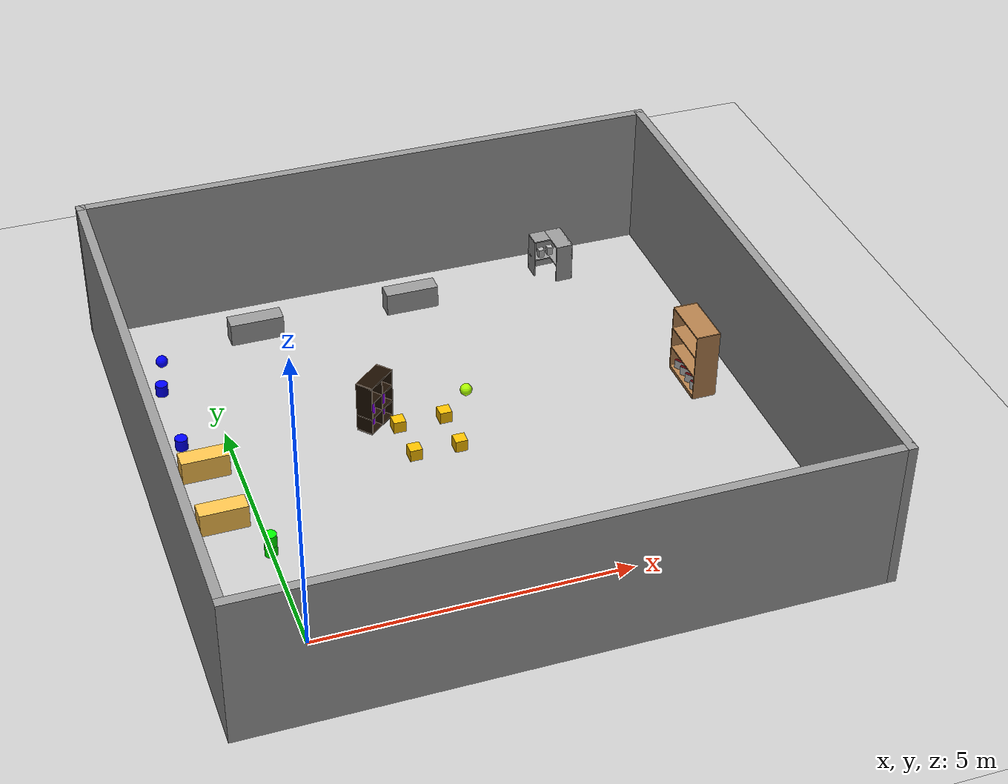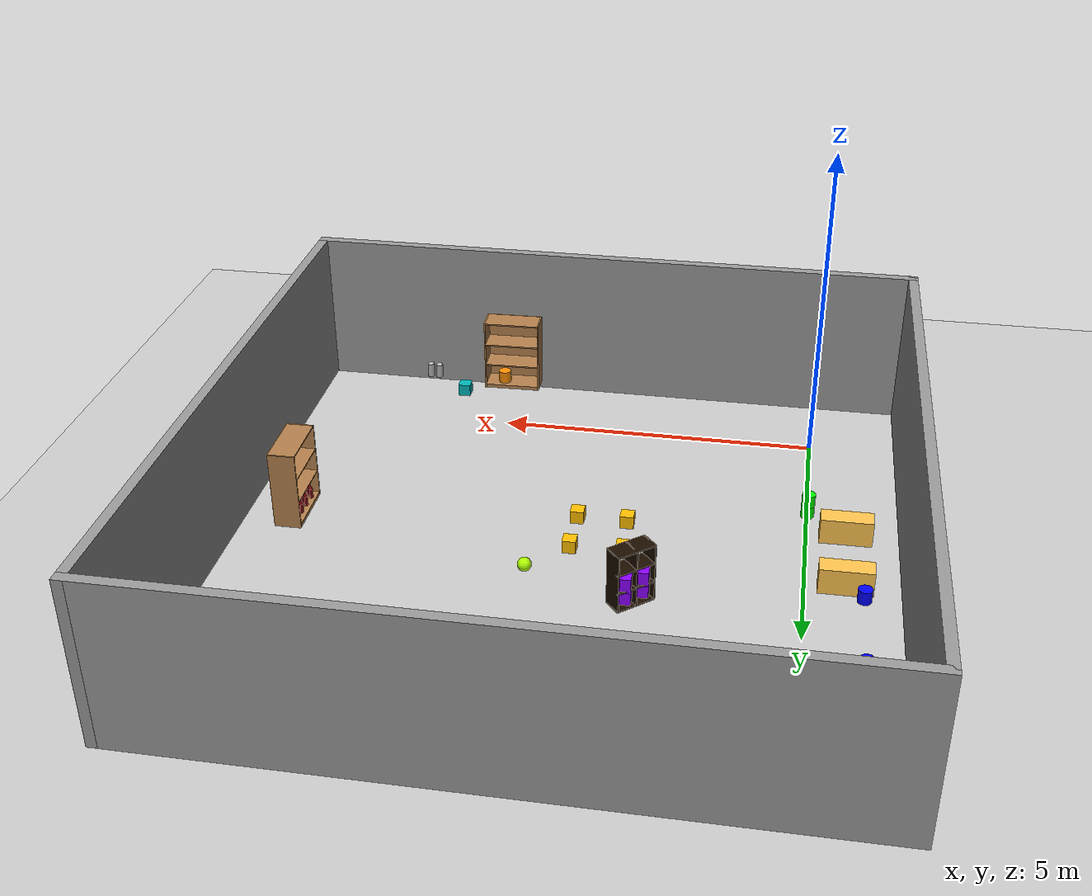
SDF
<sdf version="1.7">
 <world name="default">
  <light name="sun" type="directional">
   <pose>0 0 10 0 -0 0</pose>
   <diffuse>0.8 0.8 0.8 1</diffuse>
   <specular>0.2 0.2 0.2 1</specular>
   <attenuation>
    <range>1000</range>
    <constant>0.9</constant>
    <linear>0.01</linear>
    <quadratic>0.001</quadratic>
   </attenuation>
   <direction>-0.5 0.1 -0.9</direction>
   <spot><inner_angle>0</inner_angle><outer_angle>0</outer_angle><falloff>0</falloff></spot>
  </light>
  <model name="ground_plane">
   <static>1</static>
   <link name="link">
    <collision name="collision">
     <geometry><plane><normal>0 0 1</normal><size>100 100</size></plane></geometry>
     <surface>
      <contact><collide_bitmask>65535</collide_bitmask></contact>
      <friction><ode><mu>100</mu><mu2>50</mu2></ode></friction>
     </surface>
    </collision>
    <visual name="visual">
     <cast_shadows>0</cast_shadows>
     <geometry><plane><normal>0 0 1</normal><size>100 100</size></plane></geometry>
     <material>
      <script><uri>file://media/materials/scripts/gazebo.material</uri><name>Gazebo/Grey</name></script>
     </material>
    </visual>
   </link>
  </model>
  <gravity>0 0 -9.8</gravity>
  <magnetic_field>6e-06 2.3e-05 -4.2e-05</magnetic_field>
  <atmosphere type="adiabatic"/>
  <physics type="ode">
   <max_step_size>0.001</max_step_size>
   <real_time_factor>1</real_time_factor>
   <real_time_update_rate>1000</real_time_update_rate>
  </physics>
  <scene><ambient>0.4 0.4 0.4 1</ambient><background>0.7 0.7 0.7 1</background><shadows>1</shadows></scene>
  <spherical_coordinates>
   <surface_model>EARTH_WGS84</surface_model>
   <latitude_deg>0</latitude_deg>
   <longitude_deg>0</longitude_deg>
   <elevation>0</elevation>
   <heading_deg>0</heading_deg>
  </spherical_coordinates>
  <model name="walls">
   <pose>3.5 3.5 0 0 -0 0</pose>
   <link name="Wall_2">
    <collision name="Wall_2_Collision">
     <geometry><box><size>10 0.15 2.5</size></box></geometry>
     <pose>0 0 1.25 0 -0 0</pose>
    </collision>
    <visual name="Wall_2_Visual">
     <pose>0 0 1.25 0 -0 0</pose>
     <geometry><box><size>10 0.15 2.5</size></box></geometry>
     <material>
      <script><uri>file://media/materials/scripts/gazebo.material</uri><name>Gazebo/Grey</name></script>
      <ambient>1 1 1 1</ambient>
     </material>
     <meta><layer>0</layer></meta>
    </visual>
    <pose>0 4.925 0 0 -0 3.14159</pose>
   </link>
   <link name="Wall_3">
    <collision name="Wall_3_Collision">
     <geometry><box><size>10 0.15 2.5</size></box></geometry>
     <pose>0 0 1.25 0 -0 0</pose>
    </collision>
    <visual name="Wall_3_Visual">
     <pose>0 0 1.25 0 -0 0</pose>
     <geometry><box><size>10 0.15 2.5</size></box></geometry>
     <material>
      <script><uri>file://media/materials/scripts/gazebo.material</uri><name>Gazebo/Grey</name></script>
      <ambient>1 1 1 1</ambient>
     </material>
     <meta><layer>0</layer></meta>
    </visual>
    <pose>-4.925 0 0 0 -0 -1.5708</pose>
   </link>
   <link name="Wall_5">
    <collision name="Wall_5_Collision">
     <geometry><box><size>10 0.15 2.5</size></box></geometry>
     <pose>0 0 1.25 0 -0 0</pose>
    </collision>
    <visual name="Wall_5_Visual">
     <pose>0 0 1.25 0 -0 0</pose>
     <geometry><box><size>10 0.15 2.5</size></box></geometry>
     <material>
      <script><uri>file://media/materials/scripts/gazebo.material</uri><name>Gazebo/Grey</name></script>
      <ambient>1 1 1 1</ambient>
     </material>
     <meta><layer>0</layer></meta>
    </visual>
    <pose>0 -4.925 0 0 -0 0</pose>
   </link>
   <link name="Wall_6">
    <collision name="Wall_6_Collision">
     <geometry><box><size>10 0.15 2.5</size></box></geometry>
     <pose>0 0 1.25 0 -0 0</pose>
    </collision>
    <visual name="Wall_6_Visual">
     <pose>0 0 1.25 0 -0 0</pose>
     <geometry><box><size>10 0.15 2.5</size></box></geometry>
     <material>
      <script><uri>file://media/materials/scripts/gazebo.material</uri><name>Gazebo/Grey</name></script>
      <ambient>1 1 1 1</ambient>
     </material>
     <meta><layer>0</layer></meta>
    </visual>
    <pose>4.925 0 0 0 -0 1.5708</pose>
   </link>
   <static>1</static>
  </model>
  <model name="bookshelf">
   <static>1</static>
   <link name="link">
    <inertial><mass>1</mass></inertial>
    <collision name="back">
     <pose>0 0.005 0.6 0 -0 0</pose>
     <geometry><box><size>0.9 0.01 1.2</size></box></geometry>
    </collision>
    <visual name="visual1">
     <pose>0 0.005 0.6 0 -0 0</pose>
     <geometry><box><size>0.9 0.01 1.2</size></box></geometry>
     <material>
      <script><uri>file://media/materials/scripts/gazebo.material</uri><name>Gazebo/Wood</name></script>
     </material>
    </visual>
    <collision name="left_side">
     <pose>0.45 -0.195 0.6 0 -0 0</pose>
     <geometry><box><size>0.02 0.4 1.2</size></box></geometry>
    </collision>
    <visual name="visual2">
     <pose>0.45 -0.195 0.6 0 -0 0</pose>
     <geometry><box><size>0.02 0.4 1.2</size></box></geometry>
     <material>
      <script><uri>file://media/materials/scripts/gazebo.material</uri><name>Gazebo/Wood</name></script>
     </material>
    </visual>
    <collision name="right_side">
     <pose>-0.45 -0.195 0.6 0 -0 0</pose>
     <geometry><box><size>0.02 0.4 1.2</size></box></geometry>
    </collision>
    <visual name="visual3">
     <pose>-0.45 -0.195 0.6 0 -0 0</pose>
     <geometry><box><size>0.02 0.4 1.2</size></box></geometry>
     <material>
      <script><uri>file://media/materials/scripts/gazebo.material</uri><name>Gazebo/Wood</name></script>
     </material>
    </visual>
    <collision name="bottom">
     <pose>0 -0.195 0.03 0 -0 0</pose>
     <geometry><box><size>0.88 0.4 0.06</size></box></geometry>
    </collision>
    <visual name="visual4">
     <pose>0 -0.195 0.03 0 -0 0</pose>
     <geometry><box><size>0.88 0.4 0.06</size></box></geometry>
     <material>
      <script><uri>file://media/materials/scripts/gazebo.material</uri><name>Gazebo/Wood</name></script>
     </material>
    </visual>
    <collision name="top">
     <pose>0 -0.195 1.19 0 -0 0</pose>
     <geometry><box><size>0.88 0.4 0.02</size></box></geometry>
    </collision>
    <visual name="visual5">
     <pose>0 -0.195 1.19 0 -0 0</pose>
     <geometry><box><size>0.88 0.4 0.02</size></box></geometry>
     <material>
      <script><uri>file://media/materials/scripts/gazebo.material</uri><name>Gazebo/Wood</name></script>
     </material>
    </visual>
    <collision name="low_shelf">
     <pose>0 -0.195 0.43 0 -0 0</pose>
     <geometry><box><size>0.88 0.4 0.02</size></box></geometry>
    </collision>
    <visual name="visual6">
     <pose>0 -0.195 0.43 0 -0 0</pose>
     <geometry><box><size>0.88 0.4 0.02</size></box></geometry>
     <material>
      <script><uri>file://media/materials/scripts/gazebo.material</uri><name>Gazebo/Wood</name></script>
     </material>
    </visual>
    <collision name="high_shelf">
     <pose>0 -0.195 0.8 0 -0 0</pose>
     <geometry><box><size>0.88 0.4 0.02</size></box></geometry>
    </collision>
    <visual name="visual7">
     <pose>0 -0.195 0.8 0 -0 0</pose>
     <geometry><box><size>0.88 0.4 0.02</size></box></geometry>
     <material>
      <script><uri>file://media/materials/scripts/gazebo.material</uri><name>Gazebo/Wood</name></script>
     </material>
    </visual>
   </link>
   <pose>7.64615 3.54424 0.314432 0 0 -1.56236</pose>
  </model>
  <model name="bookshelf_clone">
   <static>1</static>
   <link name="link">
    <inertial><mass>1</mass></inertial>
    <collision name="back">
     <pose>0 0.005 0.6 0 -0 0</pose>
     <geometry><box><size>0.9 0.01 1.2</size></box></geometry>
    </collision>
    <visual name="visual1">
     <pose>0 0.005 0.6 0 -0 0</pose>
     <geometry><box><size>0.9 0.01 1.2</size></box></geometry>
     <material>
      <script><uri>file://media/materials/scripts/gazebo.material</uri><name>Gazebo/Wood</name></script>
     </material>
    </visual>
    <collision name="left_side">
     <pose>0.45 -0.195 0.6 0 -0 0</pose>
     <geometry><box><size>0.02 0.4 1.2</size></box></geometry>
    </collision>
    <visual name="visual2">
     <pose>0.45 -0.195 0.6 0 -0 0</pose>
     <geometry><box><size>0.02 0.4 1.2</size></box></geometry>
     <material>
      <script><uri>file://media/materials/scripts/gazebo.material</uri><name>Gazebo/Wood</name></script>
     </material>
    </visual>
    <collision name="right_side">
     <pose>-0.45 -0.195 0.6 0 -0 0</pose>
     <geometry><box><size>0.02 0.4 1.2</size></box></geometry>
    </collision>
    <visual name="visual3">
     <pose>-0.45 -0.195 0.6 0 -0 0</pose>
     <geometry><box><size>0.02 0.4 1.2</size></box></geometry>
     <material>
      <script><uri>file://media/materials/scripts/gazebo.material</uri><name>Gazebo/Wood</name></script>
     </material>
    </visual>
    <collision name="bottom">
     <pose>0 -0.195 0.03 0 -0 0</pose>
     <geometry><box><size>0.88 0.4 0.06</size></box></geometry>
    </collision>
    <visual name="visual4">
     <pose>0 -0.195 0.03 0 -0 0</pose>
     <geometry><box><size>0.88 0.4 0.06</size></box></geometry>
     <material>
      <script><uri>file://media/materials/scripts/gazebo.material</uri><name>Gazebo/Wood</name></script>
     </material>
    </visual>
    <collision name="top">
     <pose>0 -0.195 1.19 0 -0 0</pose>
     <geometry><box><size>0.88 0.4 0.02</size></box></geometry>
    </collision>
    <visual name="visual5">
     <pose>0 -0.195 1.19 0 -0 0</pose>
     <geometry><box><size>0.88 0.4 0.02</size></box></geometry>
     <material>
      <script><uri>file://media/materials/scripts/gazebo.material</uri><name>Gazebo/Wood</name></script>
     </material>
    </visual>
    <collision name="low_shelf">
     <pose>0 -0.195 0.43 0 -0 0</pose>
     <geometry><box><size>0.88 0.4 0.02</size></box></geometry>
    </collision>
    <visual name="visual6">
     <pose>0 -0.195 0.43 0 -0 0</pose>
     <geometry><box><size>0.88 0.4 0.02</size></box></geometry>
     <material>
      <script><uri>file://media/materials/scripts/gazebo.material</uri><name>Gazebo/Wood</name></script>
     </material>
    </visual>
    <collision name="high_shelf">
     <pose>0 -0.195 0.8 0 -0 0</pose>
     <geometry><box><size>0.88 0.4 0.02</size></box></geometry>
    </collision>
    <visual name="visual7">
     <pose>0 -0.195 0.8 0 -0 0</pose>
     <geometry><box><size>0.88 0.4 0.02</size></box></geometry>
     <material>
      <script><uri>file://media/materials/scripts/gazebo.material</uri><name>Gazebo/Wood</name></script>
     </material>
    </visual>
   </link>
   <pose>5.06709 -1.09469 0.277822 0 0 -3.11789</pose>
  </model>
  <model name="Wall_Cabinet_Coin_24x30W">
   <link name="Wall_10">
    <pose>0.286 -0.148 0.384 0 -0 0</pose>
    <inertial>
     <mass>2.1259</mass>
     <inertia><ixx>0.0158</ixx><iyy>0.1202</iyy><izz>0.1046</izz><ixy>0</ixy><ixz>0</ixz><iyz>0</iyz></inertia>
    </inertial>
    <collision name="Wall_10_Collision"><geometry><box><size>0.02 0.296 0.768</size></box></geometry></collision>
    <visual name="Wall_10_Visual">
     <geometry><box><size>0.02 0.296 0.768</size></box></geometry>
     <material>
      <script><uri>file://media/materials/scripts/gazebo.material</uri><name>Gazebo/Grey</name></script>
      <ambient>1 1 1 1</ambient>
     </material>
    </visual>
   </link>
   <joint name="10_16" type="fixed">
    <pose>0 0 -0.374 0 -0 0</pose>
    <parent>Wall_16</parent>
    <child>Wall_10</child>
    <axis><xyz>1 0 0</xyz><limit><lower>-1e+16</lower><upper>1e+16</upper></limit></axis>
   </joint>
   <joint name="10_14" type="fixed">
    <parent>Wall_14</parent>
    <child>Wall_10</child>
    <axis><xyz>1 0 0</xyz><limit><lower>-1e+16</lower><upper>1e+16</upper></limit></axis>
   </joint>
   <joint name="10_12" type="fixed">
    <pose>0 0 0.374 0 -0 0</pose>
    <parent>Wall_12</parent>
    <child>Wall_10</child>
    <axis><xyz>1 0 0</xyz><limit><lower>-1e+16</lower><upper>1e+16</upper></limit></axis>
   </joint>
   <joint name="10_29" type="fixed">
    <pose>0 -0.148 0 0 -0 0</pose>
    <parent>Wall_29</parent>
    <child>Wall_10</child>
    <axis><xyz>1 0 0</xyz><limit><lower>-1e+16</lower><upper>1e+16</upper></limit></axis>
   </joint>
   <link name="Wall_12">
    <pose>0.148 -0.148 0.758 0 -0 0</pose>
    <inertial>
     <mass>0.8802</mass>
     <inertia><ixx>0.0065</ixx><iyy>0.0139</iyy><izz>0.0074</izz><ixy>0</ixy><ixz>0</ixz><iyz>0</iyz></inertia>
    </inertial>
    <collision name="Wall_12_Collision"><geometry><box><size>0.296 0.296 0.02</size></box></geometry></collision>
    <visual name="Wall_12_Visual">
     <geometry><box><size>0.296 0.296 0.02</size></box></geometry>
     <material>
      <script><uri>file://media/materials/scripts/gazebo.material</uri><name>Gazebo/Grey</name></script>
      <ambient>1 1 1 1</ambient>
     </material>
    </visual>
   </link>
   <joint name="12_29" type="fixed">
    <pose>0 -0.148 0 0 -0 0</pose>
    <parent>Wall_29</parent>
    <child>Wall_12</child>
    <axis><xyz>0 0 1</xyz><limit><lower>-1e+16</lower><upper>1e+16</upper></limit></axis>
   </joint>
   <link name="Wall_14">
    <pose>0.148 -0.148 0.384 0 -0 0</pose>
    <inertial>
     <mass>0.8802</mass>
     <inertia><ixx>0.0065</ixx><iyy>0.0139</iyy><izz>0.0074</izz><ixy>0</ixy><ixz>0</ixz><iyz>0</iyz></inertia>
    </inertial>
    <collision name="Wall_14_Collision"><geometry><box><size>0.296 0.296 0.02</size></box></geometry></collision>
    <visual name="Wall_14_Visual">
     <geometry><box><size>0.296 0.296 0.02</size></box></geometry>
     <material>
      <script><uri>file://media/materials/scripts/gazebo.material</uri><name>Gazebo/Grey</name></script>
      <ambient>1 1 1 1</ambient>
     </material>
    </visual>
   </link>
   <joint name="14_29" type="fixed">
    <pose>0 -0.148 0 0 -0 0</pose>
    <parent>Wall_29</parent>
    <child>Wall_14</child>
    <axis><xyz>0 1 0</xyz><limit><lower>-1e+16</lower><upper>1e+16</upper></limit></axis>
   </joint>
   <link name="Wall_16">
    <pose>0.148 -0.148 0.01 0 -0 0</pose>
    <inertial>
     <mass>0.8802</mass>
     <inertia><ixx>0.0065</ixx><iyy>0.0139</iyy><izz>0.0074</izz><ixy>0</ixy><ixz>0</ixz><iyz>0</iyz></inertia>
    </inertial>
    <collision name="Wall_16_Collision"><geometry><box><size>0.296 0.296 0.02</size></box></geometry></collision>
    <visual name="Wall_16_Visual">
     <geometry><box><size>0.296 0.296 0.02</size></box></geometry>
     <material>
      <script><uri>file://media/materials/scripts/gazebo.material</uri><name>Gazebo/Grey</name></script>
      <ambient>1 1 1 1</ambient>
     </material>
    </visual>
   </link>
   <joint name="16_29" type="fixed">
    <pose>0 -0.148 0 0 -0 0</pose>
    <parent>Wall_29</parent>
    <child>Wall_16</child>
    <axis><xyz>0 1 0</xyz><limit><lower>-1e+16</lower><upper>1e+16</upper></limit></axis>
   </joint>
   <link name="Wall_18">
    <pose>-0.148 0 0.01 0 -0 0</pose>
    <inertial>
     <mass>1.6525</mass>
     <inertia><ixx>0.0491</ixx><iyy>0.0613</iyy><izz>0.0123</izz><ixy>0</ixy><ixz>0</ixz><iyz>0</iyz></inertia>
    </inertial>
    <collision name="Wall_18_Collision"><geometry><box><size>0.296 0.592 0.02</size></box></geometry></collision>
    <visual name="Wall_18_Visual">
     <geometry><box><size>0.296 0.592 0.02</size></box></geometry>
     <material>
      <script><uri>file://media/materials/scripts/gazebo.material</uri><name>Gazebo/Grey</name></script>
      <ambient>1 1 1 1</ambient>
     </material>
    </visual>
   </link>
   <joint name="18_16" type="fixed">
    <pose>0.148 -0.148 0 0 -0 0</pose>
    <parent>Wall_16</parent>
    <child>Wall_18</child>
    <axis><xyz>1 0 0</xyz><limit><lower>-1e+16</lower><upper>1e+16</upper></limit></axis>
   </joint>
   <joint name="18_29" type="fixed">
    <pose>0 -0.296 0 0 -0 0</pose>
    <parent>Wall_29</parent>
    <child>Wall_18</child>
    <axis><xyz>0 1 0</xyz><limit><lower>-1e+16</lower><upper>1e+16</upper></limit></axis>
   </joint>
   <joint name="18_27" type="fixed">
    <pose>-0.148 0 0 0 -0 0</pose>
    <parent>Wall_27</parent>
    <child>Wall_18</child>
    <axis><xyz>1 0 0</xyz><limit><lower>-1e+16</lower><upper>1e+16</upper></limit></axis>
   </joint>
   <joint name="18_30" type="fixed">
    <pose>0 0.296 0 0 -0 0</pose>
    <parent>Wall_30</parent>
    <child>Wall_18</child>
    <axis><xyz>0 1 0</xyz><limit><lower>-1e+16</lower><upper>1e+16</upper></limit></axis>
   </joint>
   <link name="Wall_20">
    <pose>-0.148 0 0.384 0 -0 0</pose>
    <inertial>
     <mass>1.6525</mass>
     <inertia><ixx>0.0491</ixx><iyy>0.0613</iyy><izz>0.0123</izz><ixy>0</ixy><ixz>0</ixz><iyz>0</iyz></inertia>
    </inertial>
    <collision name="Wall_20_Collision"><geometry><box><size>0.296 0.592 0.02</size></box></geometry></collision>
    <visual name="Wall_20_Visual">
     <geometry><box><size>0.296 0.592 0.02</size></box></geometry>
     <material>
      <script><uri>file://media/materials/scripts/gazebo.material</uri><name>Gazebo/Grey</name></script>
      <ambient>1 1 1 1</ambient>
     </material>
    </visual>
   </link>
   <joint name="20_14" type="fixed">
    <pose>0.148 -0.148 0 0 -0 0</pose>
    <parent>Wall_14</parent>
    <child>Wall_20</child>
    <axis><xyz>1 0 0</xyz><limit><lower>-1e+16</lower><upper>1e+16</upper></limit></axis>
   </joint>
   <joint name="20_29" type="fixed">
    <pose>0 -0.296 0 0 -0 0</pose>
    <parent>Wall_29</parent>
    <child>Wall_20</child>
    <axis><xyz>0 1 0</xyz><limit><lower>-1e+16</lower><upper>1e+16</upper></limit></axis>
   </joint>
   <joint name="20_27" type="fixed">
    <pose>-0.148 0 0 0 -0 0</pose>
    <parent>Wall_27</parent>
    <child>Wall_20</child>
    <axis><xyz>1 0 0</xyz><limit><lower>-1e+16</lower><upper>1e+16</upper></limit></axis>
   </joint>
   <joint name="20_30" type="fixed">
    <pose>0 0.296 0 0 -0 0</pose>
    <parent>Wall_30</parent>
    <child>Wall_20</child>
    <axis><xyz>0 1 0</xyz><limit><lower>-1e+16</lower><upper>1e+16</upper></limit></axis>
   </joint>
   <link name="Wall_22">
    <pose>-0.148 0 0.758 0 -0 0</pose>
    <inertial>
     <mass>1.6525</mass>
     <inertia><ixx>0.0491</ixx><iyy>0.0613</iyy><izz>0.0123</izz><ixy>0</ixy><ixz>0</ixz><iyz>0</iyz></inertia>
    </inertial>
    <collision name="Wall_22_Collision"><geometry><box><size>0.296 0.592 0.02</size></box></geometry></collision>
    <visual name="Wall_22_Visual">
     <geometry><box><size>0.296 0.592 0.02</size></box></geometry>
     <material>
      <script><uri>file://media/materials/scripts/gazebo.material</uri><name>Gazebo/Grey</name></script>
      <ambient>1 1 1 1</ambient>
     </material>
    </visual>
   </link>
   <joint name="22_12" type="fixed">
    <pose>0.148 -0.148 0 0 -0 0</pose>
    <parent>Wall_12</parent>
    <child>Wall_22</child>
    <axis><xyz>1 0 0</xyz><limit><lower>-1e+16</lower><upper>1e+16</upper></limit></axis>
   </joint>
   <joint name="22_29" type="fixed">
    <pose>0 -0.296 0 0 -0 0</pose>
    <parent>Wall_29</parent>
    <child>Wall_22</child>
    <axis><xyz>0 1 0</xyz><limit><lower>-1e+16</lower><upper>1e+16</upper></limit></axis>
   </joint>
   <joint name="22_27" type="fixed">
    <pose>-0.148 0 0 0 -0 0</pose>
    <parent>Wall_27</parent>
    <child>Wall_22</child>
    <axis><xyz>1 0 0</xyz><limit><lower>-1e+16</lower><upper>1e+16</upper></limit></axis>
   </joint>
   <joint name="22_30" type="fixed">
    <pose>0 0.296 0 0 -0 0</pose>
    <parent>Wall_30</parent>
    <child>Wall_22</child>
    <axis><xyz>0 1 0</xyz><limit><lower>-1e+16</lower><upper>1e+16</upper></limit></axis>
   </joint>
   <link name="Wall_27">
    <pose>-0.286 0 0.384 0 -0 0</pose>
    <inertial>
     <mass>4.2589</mass>
     <inertia><ixx>0.1266</ixx><iyy>0.3358</iyy><izz>0.2095</izz><ixy>0</ixy><ixz>0</ixz><iyz>0</iyz></inertia>
    </inertial>
    <collision name="Wall_27_Collision"><geometry><box><size>0.02 0.592 0.768</size></box></geometry></collision>
    <visual name="Wall_27_Visual">
     <geometry><box><size>0.02 0.592 0.768</size></box></geometry>
     <material>
      <script><uri>file://media/materials/scripts/gazebo.material</uri><name>Gazebo/Grey</name></script>
      <ambient>1 1 1 1</ambient>
     </material>
    </visual>
   </link>
   <joint name="27_30" type="fixed">
    <pose>0 0.296 0 0 -0 0</pose>
    <parent>Wall_30</parent>
    <child>Wall_27</child>
    <axis><xyz>0 1 0</xyz><limit><lower>-1e+16</lower><upper>1e+16</upper></limit></axis>
   </joint>
   <link name="Wall_29">
    <pose>0 -0.286 0.384 0 -0 0</pose>
    <inertial>
     <mass>4.3176</mass>
     <inertia><ixx>0.134</ixx><iyy>0.2091</iyy><izz>0.3428</izz><ixy>0</ixy><ixz>0</ixz><iyz>0</iyz></inertia>
    </inertial>
    <collision name="Wall_29_Collision"><geometry><box><size>0.592 0.02 0.768</size></box></geometry></collision>
    <visual name="Wall_29_Visual">
     <geometry><box><size>0.592 0.02 0.768</size></box></geometry>
     <material>
      <script><uri>file://media/materials/scripts/gazebo.material</uri><name>Gazebo/Grey</name></script>
      <ambient>1 1 1 1</ambient>
     </material>
    </visual>
   </link>
   <link name="Wall_30">
    <pose>-0.148 0.286 0.384 0 -0 0</pose>
    <inertial>
     <mass>2.1093</mass>
     <inertia><ixx>0.1021</ixx><iyy>0.0157</iyy><izz>0.1177</izz><ixy>0</ixy><ixz>0</ixz><iyz>0</iyz></inertia>
    </inertial>
    <collision name="Wall_30_Collision"><geometry><box><size>0.296 0.02 0.768</size></box></geometry></collision>
    <visual name="Wall_30_Visual">
     <geometry><box><size>0.296 0.02 0.768</size></box></geometry>
     <material>
      <script><uri>file://media/materials/scripts/gazebo.material</uri><name>Gazebo/Grey</name></script>
      <ambient>1 1 1 1</ambient>
     </material>
    </visual>
   </link>
   <static>1</static>
   <pose>6.53795 7.67148 -0.076235 0 0 -3.11243</pose>
  </model>
  <model name="cylinder_o">
   <link name="link_0">
    <pose>0 0 0.1 0 -0 0</pose>
    <inertial>
     <mass>1</mass>
     <inertia><ixx>0.145833</ixx><ixy>0</ixy><ixz>0</ixz><iyy>0.145833</iyy><iyz>0</iyz><izz>0.125</izz></inertia>
    </inertial>
    <visual name="visual">
     <geometry><cylinder><radius>0.1</radius><length>0.2</length></cylinder></geometry>
     <material>
      <lighting>1</lighting>
      <script><uri>file://media/materials/scripts/gazebo.material</uri><name>Gazebo/Grey</name></script>
      <ambient>1 0.561 0 1</ambient>
      <diffuse>1 0.561 0 1</diffuse>
      <specular>0 0 0 1</specular>
      <emissive>0 0 0 1</emissive>
      <shader type="vertex"><normal_map>__default__</normal_map></shader>
     </material>
    </visual>
    <collision name="collision">
     <geometry><cylinder><radius>0.1</radius><length>0.2</length></cylinder></geometry>
     <surface>
      <friction>
       <ode><mu>1</mu><mu2>1</mu2><fdir1>0 0 0</fdir1><slip1>0</slip1><slip2>0</slip2></ode>
       <torsional>
        <coefficient>1</coefficient>
        <patch_radius>0</patch_radius>
        <surface_radius>0</surface_radius>
        <use_patch_radius>1</use_patch_radius>
        <ode><slip>0</slip></ode>
       </torsional>
      </friction>
      <bounce><restitution_coefficient>0</restitution_coefficient><threshold>1e+06</threshold></bounce>
      <contact>
       <collide_without_contact>0</collide_without_contact>
       <collide_without_contact_bitmask>1</collide_without_contact_bitmask>
       <collide_bitmask>1</collide_bitmask>
       <ode>
        <soft_cfm>0</soft_cfm>
        <soft_erp>0.2</soft_erp>
        <kp>1e+13</kp>
        <kd>1</kd>
        <max_vel>0.01</max_vel>
        <min_depth>0</min_depth>
       </ode>
       <bullet>
        <split_impulse>1</split_impulse>
        <split_impulse_penetration_threshold>-0.01</split_impulse_penetration_threshold>
        <soft_cfm>0</soft_cfm>
        <soft_erp>0.2</soft_erp>
        <kp>1e+13</kp>
        <kd>1</kd>
       </bullet>
      </contact>
     </surface>
    </collision>
   </link>
   <static>1</static>
   <pose>5.20056 -0.842371 0.344102 0 -0 0</pose>
  </model>
  <model name="beer">
   <link name="link">
    <pose>0 0 0.115 0 -0 0</pose>
    <inertial>
     <mass>0.39</mass>
     <inertia><ixx>0.00058</ixx><ixy>0</ixy><ixz>0</ixz><iyy>0.00058</iyy><iyz>0</iyz><izz>0.00019</izz></inertia>
    </inertial>
    <collision name="collision">
     <geometry><cylinder><radius>0.055</radius><length>0.23</length></cylinder></geometry>
    </collision>
    <visual name="visual">
     <geometry><cylinder><radius>0.055</radius><length>0.23</length></cylinder></geometry>
     <material>
      <script>
       <uri>model://beer/materials/scripts</uri>
       <uri>model://beer/materials/textures</uri>
       <name>Beer/Diffuse</name>
      </script>
     </material>
    </visual>
   </link>
   <pose>6.50408 -0.857973 0.329521 8e-06 1.8e-05 0.018777</pose>
  </model>
  <model name="beer_0">
   <link name="link">
    <pose>0 0 0.115 0 -0 0</pose>
    <inertial>
     <mass>0.39</mass>
     <inertia><ixx>0.00058</ixx><ixy>0</ixy><ixz>0</ixz><iyy>0.00058</iyy><iyz>0</iyz><izz>0.00019</izz></inertia>
    </inertial>
    <collision name="collision">
     <geometry><cylinder><radius>0.055</radius><length>0.23</length></cylinder></geometry>
    </collision>
    <visual name="visual">
     <geometry><cylinder><radius>0.055</radius><length>0.23</length></cylinder></geometry>
     <material>
      <script>
       <uri>model://beer/materials/scripts</uri>
       <uri>model://beer/materials/textures</uri>
       <name>Beer/Diffuse</name>
      </script>
     </material>
    </visual>
   </link>
   <pose>6.35605 -0.850127 0.329512 1e-06 -2.7e-05 0.006479</pose>
  </model>
  <model name="tea_box">
   <link name="link">
    <pose>0 0 0.075 0 -0 0</pose>
    <visual name="visual">
     <geometry><box><size>0.1 0.1 0.15</size></box></geometry>
     <material>
      <script>
       <uri>model://tea_box/materials/scripts</uri>
       <uri>model://tea_box/materials/textures</uri>
       <name>tea_pat</name>
      </script>
     </material>
    </visual>
    <collision name="collision"><geometry><box><size>0.1 0.1 0.15</size></box></geometry></collision>
   </link>
   <static>1</static>
   <pose>6.3937 7.76277 0.31356 0 -0 0</pose>
  </model>
  <model name="tea_box_clone">
   <link name="link">
    <pose>0 0 0.075 0 -0 0</pose>
    <visual name="visual">
     <geometry><box><size>0.1 0.1 0.15</size></box></geometry>
     <material>
      <script>
       <uri>model://tea_box/materials/scripts</uri>
       <uri>model://tea_box/materials/textures</uri>
       <name>tea_pat</name>
      </script>
     </material>
    </visual>
    <collision name="collision"><geometry><box><size>0.1 0.1 0.15</size></box></geometry></collision>
   </link>
   <static>1</static>
   <pose>6.56471 7.79411 0.314783 0 -0 0</pose>
  </model>
  <model name="coffee_box">
   <link name="link_0">
    <visual name="visual">
     <pose>0 0 0.06 0 -0 0</pose>
     <geometry><cylinder><radius>0.04</radius><length>0.12</length></cylinder></geometry>
     <material>
      <script>
       <uri>model://coffee_box/materials/scripts</uri>
       <uri>model://coffee_box/materials/textures</uri>
       <name>coffee_pat</name>
      </script>
     </material>
    </visual>
    <collision name="collision">
     <geometry><cylinder><radius>0.04</radius><length>0.12</length></cylinder></geometry>
    </collision>
   </link>
   <static>1</static>
   <pose>6.67443 7.49279 0.308834 0 -0 0</pose>
  </model>
  <model name="biscuit_box">
   <link name="link">
    <pose>0 0 0.025 0 -0 0</pose>
    <visual name="visual">
     <geometry><box><size>0.2 0.15 0.05</size></box></geometry>
     <material>
      <ambient>0.423 0.019 0.035 1</ambient>
      <diffuse>0.423 0.019 0.035 1</diffuse>
      <specular>0.01 0.01 0.01 1</specular>
      <emissive>0 0 0 1</emissive>
     </material>
    </visual>
    <collision name="collision"><geometry><box><size>0.1 0.1 0.15</size></box></geometry></collision>
   </link>
   <link name="link_1">
    <pose>0 0 0.05 0 -0 0</pose>
    <visual name="visual">
     <geometry><box><size>0.2 0.15 0.001</size></box></geometry>
     <material>
      <script>
       <uri>model://biscuit_box/materials/scripts</uri>
       <uri>model://biscuit_box/materials/textures</uri>
       <name>biscuit_pat</name>
      </script>
     </material>
    </visual>
    <collision name="collision"><geometry><box><size>0.1 0.1 0.15</size></box></geometry></collision>
   </link>
   <static>1</static>
   <pose>7.39517 3.64518 0.451865 1.57021 -0.00085 -0.969106</pose>
  </model>
  <model name="biscuit_box_clone">
   <link name="link">
    <pose>0 0 0.025 0 -0 0</pose>
    <visual name="visual">
     <geometry><box><size>0.2 0.15 0.05</size></box></geometry>
     <material>
      <ambient>0.423 0.019 0.035 1</ambient>
      <diffuse>0.423 0.019 0.035 1</diffuse>
      <specular>0.01 0.01 0.01 1</specular>
      <emissive>0 0 0 1</emissive>
     </material>
    </visual>
    <collision name="collision"><geometry><box><size>0.1 0.1 0.15</size></box></geometry></collision>
   </link>
   <link name="link_1">
    <pose>0 0 0.05 0 -0 0</pose>
    <visual name="visual">
     <geometry><box><size>0.2 0.15 0.001</size></box></geometry>
     <material>
      <script>
       <uri>model://biscuit_box/materials/scripts</uri>
       <uri>model://biscuit_box/materials/textures</uri>
       <name>biscuit_pat</name>
      </script>
     </material>
    </visual>
    <collision name="collision"><geometry><box><size>0.1 0.1 0.15</size></box></geometry></collision>
   </link>
   <static>1</static>
   <pose>7.38449 3.83821 0.451865 1.57021 -0.00085 -0.969106</pose>
  </model>
  <model name="biscuit_box_clone_0">
   <link name="link">
    <pose>0 0 0.025 0 -0 0</pose>
    <visual name="visual">
     <geometry><box><size>0.2 0.15 0.05</size></box></geometry>
     <material>
      <ambient>0.423 0.019 0.035 1</ambient>
      <diffuse>0.423 0.019 0.035 1</diffuse>
      <specular>0.01 0.01 0.01 1</specular>
      <emissive>0 0 0 1</emissive>
     </material>
    </visual>
    <collision name="collision"><geometry><box><size>0.1 0.1 0.15</size></box></geometry></collision>
   </link>
   <link name="link_1">
    <pose>0 0 0.05 0 -0 0</pose>
    <visual name="visual">
     <geometry><box><size>0.2 0.15 0.001</size></box></geometry>
     <material>
      <script>
       <uri>model://biscuit_box/materials/scripts</uri>
       <uri>model://biscuit_box/materials/textures</uri>
       <name>biscuit_pat</name>
      </script>
     </material>
    </visual>
    <collision name="collision"><geometry><box><size>0.1 0.1 0.15</size></box></geometry></collision>
   </link>
   <static>1</static>
   <pose>7.39578 3.44511 0.451865 1.57021 -0.00085 -0.969106</pose>
  </model>
  <model name="biscuit_box_clone_1">
   <link name="link">
    <pose>0 0 0.025 0 -0 0</pose>
    <visual name="visual">
     <geometry><box><size>0.2 0.15 0.05</size></box></geometry>
     <material>
      <ambient>0.423 0.019 0.035 1</ambient>
      <diffuse>0.423 0.019 0.035 1</diffuse>
      <specular>0.01 0.01 0.01 1</specular>
      <emissive>0 0 0 1</emissive>
     </material>
    </visual>
    <collision name="collision"><geometry><box><size>0.1 0.1 0.15</size></box></geometry></collision>
   </link>
   <link name="link_1">
    <pose>0 0 0.05 0 -0 0</pose>
    <visual name="visual">
     <geometry><box><size>0.2 0.15 0.001</size></box></geometry>
     <material>
      <script>
       <uri>model://biscuit_box/materials/scripts</uri>
       <uri>model://biscuit_box/materials/textures</uri>
       <name>biscuit_pat</name>
      </script>
     </material>
    </visual>
    <collision name="collision"><geometry><box><size>0.1 0.1 0.15</size></box></geometry></collision>
   </link>
   <static>1</static>
   <pose>7.38574 3.23303 0.451865 1.57021 -0.00085 -0.969106</pose>
  </model>
  <model name="cylinder_b">
   <link name="link_0">
    <pose>0 0 0.1 0 -0 0</pose>
    <inertial>
     <mass>1</mass>
     <inertia><ixx>0.145833</ixx><ixy>0</ixy><ixz>0</ixz><iyy>0.145833</iyy><iyz>0</iyz><izz>0.125</izz></inertia>
    </inertial>
    <visual name="visual">
     <geometry><cylinder><radius>0.1</radius><length>0.2</length></cylinder></geometry>
     <material>
      <lighting>1</lighting>
      <script><uri>file://media/materials/scripts/gazebo.material</uri><name>Gazebo/Grey</name></script>
      <ambient>0 0 1 1</ambient>
      <diffuse>0 0 1 1</diffuse>
      <specular>0 0 0 1</specular>
      <emissive>0 0 0 1</emissive>
      <shader type="vertex"><normal_map>__default__</normal_map></shader>
     </material>
    </visual>
    <collision name="collision">
     <geometry><cylinder><radius>0.1</radius><length>0.2</length></cylinder></geometry>
     <surface>
      <friction>
       <ode><mu>1</mu><mu2>1</mu2><fdir1>0 0 0</fdir1><slip1>0</slip1><slip2>0</slip2></ode>
       <torsional>
        <coefficient>1</coefficient>
        <patch_radius>0</patch_radius>
        <surface_radius>0</surface_radius>
        <use_patch_radius>1</use_patch_radius>
        <ode><slip>0</slip></ode>
       </torsional>
      </friction>
      <bounce><restitution_coefficient>0</restitution_coefficient><threshold>1e+06</threshold></bounce>
      <contact>
       <collide_without_contact>0</collide_without_contact>
       <collide_without_contact_bitmask>1</collide_without_contact_bitmask>
       <collide_bitmask>1</collide_bitmask>
       <ode>
        <soft_cfm>0</soft_cfm>
        <soft_erp>0.2</soft_erp>
        <kp>1e+13</kp>
        <kd>1</kd>
        <max_vel>0.01</max_vel>
        <min_depth>0</min_depth>
       </ode>
       <bullet>
        <split_impulse>1</split_impulse>
        <split_impulse_penetration_threshold>-0.01</split_impulse_penetration_threshold>
        <soft_cfm>0</soft_cfm>
        <soft_erp>0.2</soft_erp>
        <kp>1e+13</kp>
        <kd>1</kd>
       </bullet>
      </contact>
     </surface>
    </collision>
   </link>
   <static>1</static>
   <pose>-0.792536 4.45575 0.336104 0 -0 0</pose>
  </model>
  <model name="cylinder_b_0">
   <link name="link_0">
    <pose>0 0 0.1 0 -0 0</pose>
    <inertial>
     <mass>1</mass>
     <inertia><ixx>0.145833</ixx><ixy>0</ixy><ixz>0</ixz><iyy>0.145833</iyy><iyz>0</iyz><izz>0.125</izz></inertia>
    </inertial>
    <visual name="visual">
     <geometry><cylinder><radius>0.1</radius><length>0.2</length></cylinder></geometry>
     <material>
      <lighting>1</lighting>
      <script><uri>file://media/materials/scripts/gazebo.material</uri><name>Gazebo/Grey</name></script>
      <ambient>0 0 1 1</ambient>
      <diffuse>0 0 1 1</diffuse>
      <specular>0 0 0 1</specular>
      <emissive>0 0 0 1</emissive>
      <shader type="vertex"><normal_map>__default__</normal_map></shader>
     </material>
    </visual>
    <collision name="collision">
     <geometry><cylinder><radius>0.1</radius><length>0.2</length></cylinder></geometry>
     <surface>
      <friction>
       <ode><mu>1</mu><mu2>1</mu2><fdir1>0 0 0</fdir1><slip1>0</slip1><slip2>0</slip2></ode>
       <torsional>
        <coefficient>1</coefficient>
        <patch_radius>0</patch_radius>
        <surface_radius>0</surface_radius>
        <use_patch_radius>1</use_patch_radius>
        <ode><slip>0</slip></ode>
       </torsional>
      </friction>
      <bounce><restitution_coefficient>0</restitution_coefficient><threshold>1e+06</threshold></bounce>
      <contact>
       <collide_without_contact>0</collide_without_contact>
       <collide_without_contact_bitmask>1</collide_without_contact_bitmask>
       <collide_bitmask>1</collide_bitmask>
       <ode>
        <soft_cfm>0</soft_cfm>
        <soft_erp>0.2</soft_erp>
        <kp>1e+13</kp>
        <kd>1</kd>
        <max_vel>0.01</max_vel>
        <min_depth>0</min_depth>
       </ode>
       <bullet>
        <split_impulse>1</split_impulse>
        <split_impulse_penetration_threshold>-0.01</split_impulse_penetration_threshold>
        <soft_cfm>0</soft_cfm>
        <soft_erp>0.2</soft_erp>
        <kp>1e+13</kp>
        <kd>1</kd>
       </bullet>
      </contact>
     </surface>
    </collision>
   </link>
   <static>1</static>
   <pose>-0.793247 5.92319 0.334022 0 -0 0</pose>
  </model>
  <model name="sphere_b">
   <link name="link_1">
    <pose>0 0 0.1 0 -0 0</pose>
    <inertial>
     <mass>1</mass>
     <inertia><ixx>0.1</ixx><ixy>0</ixy><ixz>0</ixz><iyy>0.1</iyy><iyz>0</iyz><izz>0.1</izz></inertia>
    </inertial>
    <visual name="visual">
     <geometry><sphere><radius>0.1</radius></sphere></geometry>
     <material>
      <lighting>1</lighting>
      <script><uri>file://media/materials/scripts/gazebo.material</uri><name>Gazebo/Grey</name></script>
      <ambient>0 0 1 1</ambient>
      <diffuse>0 0 1 1</diffuse>
      <specular>0 0 0 1</specular>
      <emissive>0 0 0 1</emissive>
      <shader type="vertex"><normal_map>__default__</normal_map></shader>
     </material>
    </visual>
    <collision name="collision">
     <geometry><sphere><radius>0.1</radius></sphere></geometry>
     <surface>
      <friction>
       <ode><mu>1</mu><mu2>1</mu2><fdir1>0 0 0</fdir1><slip1>0</slip1><slip2>0</slip2></ode>
       <torsional>
        <coefficient>1</coefficient>
        <patch_radius>0</patch_radius>
        <surface_radius>0</surface_radius>
        <use_patch_radius>1</use_patch_radius>
        <ode><slip>0</slip></ode>
       </torsional>
      </friction>
      <bounce><restitution_coefficient>0</restitution_coefficient><threshold>1e+06</threshold></bounce>
      <contact>
       <collide_without_contact>0</collide_without_contact>
       <collide_without_contact_bitmask>1</collide_without_contact_bitmask>
       <collide_bitmask>1</collide_bitmask>
       <ode>
        <soft_cfm>0</soft_cfm>
        <soft_erp>0.2</soft_erp>
        <kp>1e+13</kp>
        <kd>1</kd>
        <max_vel>0.01</max_vel>
        <min_depth>0</min_depth>
       </ode>
       <bullet>
        <split_impulse>1</split_impulse>
        <split_impulse_penetration_threshold>-0.01</split_impulse_penetration_threshold>
        <soft_cfm>0</soft_cfm>
        <soft_erp>0.2</soft_erp>
        <kp>1e+13</kp>
        <kd>1</kd>
       </bullet>
      </contact>
     </surface>
    </collision>
   </link>
   <static>1</static>
   <pose>-0.612109 6.82404 0.208521 0 -0 0</pose>
  </model>
  <model name="Box_15x30">
   <link name="Wall">
    <pose>0 0 0.1985 0 -0 0</pose>
    <inertial>
     <mass>5</mass>
     <inertia><ixx>0.3089</ixx><iyy>0.1022</iyy><izz>0.2797</izz><ixy>0</ixy><ixz>0</ixz><iyz>0</iyz></inertia>
    </inertial>
    <collision name="Wall_Collision"><geometry><box><size>0.296 0.764 0.397</size></box></geometry></collision>
    <visual name="Wall_Visual">
     <geometry><box><size>0.296 0.764 0.397</size></box></geometry>
     <material>
      <script><uri>file://media/materials/scripts/gazebo.material</uri><name>Gazebo/Grey</name></script>
      <ambient>1 0.764706 0.305882 1</ambient>
     </material>
    </visual>
   </link>
   <static>1</static>
   <pose>-0.560762 2.70227 0.120926 0 0 -1.5633</pose>
  </model>
  <model name="Box_15x30_clone">
   <link name="Wall">
    <pose>0 0 0.1985 0 -0 0</pose>
    <inertial>
     <mass>5</mass>
     <inertia><ixx>0.3089</ixx><iyy>0.1022</iyy><izz>0.2797</izz><ixy>0</ixy><ixz>0</ixz><iyz>0</iyz></inertia>
    </inertial>
    <collision name="Wall_Collision"><geometry><box><size>0.296 0.764 0.397</size></box></geometry></collision>
    <visual name="Wall_Visual">
     <geometry><box><size>0.296 0.764 0.397</size></box></geometry>
     <material>
      <script><uri>file://media/materials/scripts/gazebo.material</uri><name>Gazebo/Grey</name></script>
      <ambient>1 0.764706 0.305882 1</ambient>
     </material>
    </visual>
   </link>
   <static>1</static>
   <pose>-0.553817 3.95824 0.140204 0 0 -1.5633</pose>
  </model>
  <model name="cube_bg">
   <link name="link_2">
    <pose>0 0 0.1 0 -0 0</pose>
    <inertial>
     <mass>1</mass>
     <inertia>
      <ixx>0.166667</ixx>
      <ixy>0</ixy>
      <ixz>0</ixz>
      <iyy>0.166667</iyy>
      <iyz>0</iyz>
      <izz>0.166667</izz>
     </inertia>
    </inertial>
    <visual name="visual">
     <geometry><box><size>0.2 0.2 0.2</size></box></geometry>
     <material>
      <lighting>1</lighting>
      <script><uri>file://media/materials/scripts/gazebo.material</uri><name>Gazebo/Grey</name></script>
      <ambient>0 0.71 0.722 1</ambient>
      <diffuse>0 0.71 0.722 1</diffuse>
      <specular>0 0 0 1</specular>
      <emissive>0 0 0 1</emissive>
      <shader type="vertex"><normal_map>__default__</normal_map></shader>
     </material>
    </visual>
    <collision name="collision">
     <geometry><box><size>0.2 0.2 0.2</size></box></geometry>
     <surface>
      <friction>
       <ode><mu>1</mu><mu2>1</mu2><fdir1>0 0 0</fdir1><slip1>0</slip1><slip2>0</slip2></ode>
       <torsional>
        <coefficient>1</coefficient>
        <patch_radius>0</patch_radius>
        <surface_radius>0</surface_radius>
        <use_patch_radius>1</use_patch_radius>
        <ode><slip>0</slip></ode>
       </torsional>
      </friction>
      <bounce><restitution_coefficient>0</restitution_coefficient><threshold>1e+06</threshold></bounce>
      <contact>
       <collide_without_contact>0</collide_without_contact>
       <collide_without_contact_bitmask>1</collide_without_contact_bitmask>
       <collide_bitmask>1</collide_bitmask>
       <ode>
        <soft_cfm>0</soft_cfm>
        <soft_erp>0.2</soft_erp>
        <kp>1e+13</kp>
        <kd>1</kd>
        <max_vel>0.01</max_vel>
        <min_depth>0</min_depth>
       </ode>
       <bullet>
        <split_impulse>1</split_impulse>
        <split_impulse_penetration_threshold>-0.01</split_impulse_penetration_threshold>
        <soft_cfm>0</soft_cfm>
        <soft_erp>0.2</soft_erp>
        <kp>1e+13</kp>
        <kd>1</kd>
       </bullet>
      </contact>
     </surface>
    </collision>
   </link>
   <static>1</static>
   <pose>5.92664 -0.918341 0 0 -0 0</pose>
  </model>
  <model name="cylinder_g">
   <link name="link_0">
    <pose>0 0 0.1 0 -0 0</pose>
    <inertial>
     <mass>1</mass>
     <inertia><ixx>0.145833</ixx><ixy>0</ixy><ixz>0</ixz><iyy>0.145833</iyy><iyz>0</iyz><izz>0.125</izz></inertia>
    </inertial>
    <visual name="visual">
     <geometry><cylinder><radius>0.1</radius><length>0.2</length></cylinder></geometry>
     <material>
      <lighting>1</lighting>
      <script><uri>file://media/materials/scripts/gazebo.material</uri><name>Gazebo/Grey</name></script>
      <ambient>0 1 0 1</ambient>
      <diffuse>0 1 0 1</diffuse>
      <specular>0 0 0 1</specular>
      <emissive>0 0 0 1</emissive>
      <shader type="vertex"><normal_map>__default__</normal_map></shader>
     </material>
    </visual>
    <collision name="collision">
     <geometry><cylinder><radius>0.1</radius><length>0.2</length></cylinder></geometry>
     <surface>
      <friction>
       <ode><mu>1</mu><mu2>1</mu2><fdir1>0 0 0</fdir1><slip1>0</slip1><slip2>0</slip2></ode>
       <torsional>
        <coefficient>1</coefficient>
        <patch_radius>0</patch_radius>
        <surface_radius>0</surface_radius>
        <use_patch_radius>1</use_patch_radius>
        <ode><slip>0</slip></ode>
       </torsional>
      </friction>
      <bounce><restitution_coefficient>0</restitution_coefficient><threshold>1e+06</threshold></bounce>
      <contact>
       <collide_without_contact>0</collide_without_contact>
       <collide_without_contact_bitmask>1</collide_without_contact_bitmask>
       <collide_bitmask>1</collide_bitmask>
       <ode>
        <soft_cfm>0</soft_cfm>
        <soft_erp>0.2</soft_erp>
        <kp>1e+13</kp>
        <kd>1</kd>
        <max_vel>0.01</max_vel>
        <min_depth>0</min_depth>
       </ode>
       <bullet>
        <split_impulse>1</split_impulse>
        <split_impulse_penetration_threshold>-0.01</split_impulse_penetration_threshold>
        <soft_cfm>0</soft_cfm>
        <soft_erp>0.2</soft_erp>
        <kp>1e+13</kp>
        <kd>1</kd>
       </bullet>
      </contact>
     </surface>
    </collision>
   </link>
   <static>1</static>
   <pose>-0.008504 1.99028 0.192879 0 -0 0</pose>
  </model>
  <model name="cylinder_g_clone">
   <link name="link_0">
    <pose>0 0 0.1 0 -0 0</pose>
    <inertial>
     <mass>1</mass>
     <inertia><ixx>0.145833</ixx><ixy>0</ixy><ixz>0</ixz><iyy>0.145833</iyy><iyz>0</iyz><izz>0.125</izz></inertia>
    </inertial>
    <visual name="visual">
     <geometry><cylinder><radius>0.1</radius><length>0.2</length></cylinder></geometry>
     <material>
      <lighting>1</lighting>
      <script><uri>file://media/materials/scripts/gazebo.material</uri><name>Gazebo/Grey</name></script>
      <ambient>0 1 0 1</ambient>
      <diffuse>0 1 0 1</diffuse>
      <specular>0 0 0 1</specular>
      <emissive>0 0 0 1</emissive>
      <shader type="vertex"><normal_map>__default__</normal_map></shader>
     </material>
    </visual>
    <collision name="collision">
     <geometry><cylinder><radius>0.1</radius><length>0.2</length></cylinder></geometry>
     <surface>
      <friction>
       <ode><mu>1</mu><mu2>1</mu2><fdir1>0 0 0</fdir1><slip1>0</slip1><slip2>0</slip2></ode>
       <torsional>
        <coefficient>1</coefficient>
        <patch_radius>0</patch_radius>
        <surface_radius>0</surface_radius>
        <use_patch_radius>1</use_patch_radius>
        <ode><slip>0</slip></ode>
       </torsional>
      </friction>
      <bounce><restitution_coefficient>0</restitution_coefficient><threshold>1e+06</threshold></bounce>
      <contact>
       <collide_without_contact>0</collide_without_contact>
       <collide_without_contact_bitmask>1</collide_without_contact_bitmask>
       <collide_bitmask>1</collide_bitmask>
       <ode>
        <soft_cfm>0</soft_cfm>
        <soft_erp>0.2</soft_erp>
        <kp>1e+13</kp>
        <kd>1</kd>
        <max_vel>0.01</max_vel>
        <min_depth>0</min_depth>
       </ode>
       <bullet>
        <split_impulse>1</split_impulse>
        <split_impulse_penetration_threshold>-0.01</split_impulse_penetration_threshold>
        <soft_cfm>0</soft_cfm>
        <soft_erp>0.2</soft_erp>
        <kp>1e+13</kp>
        <kd>1</kd>
       </bullet>
      </contact>
     </surface>
    </collision>
   </link>
   <static>1</static>
   <pose>-0.008504 1.99028 0 0 -0 0</pose>
  </model>
  <model name="cube_yo">
   <link name="link_2">
    <pose>0 0 0.1 0 -0 0</pose>
    <inertial>
     <mass>1</mass>
     <inertia>
      <ixx>0.166667</ixx>
      <ixy>0</ixy>
      <ixz>0</ixz>
      <iyy>0.166667</iyy>
      <iyz>0</iyz>
      <izz>0.166667</izz>
     </inertia>
    </inertial>
    <visual name="visual">
     <geometry><box><size>0.2 0.2 0.2</size></box></geometry>
     <material>
      <lighting>1</lighting>
      <script><uri>file://media/materials/scripts/gazebo.material</uri><name>Gazebo/Grey</name></script>
      <ambient>1 0.749 0 1</ambient>
      <diffuse>1 0.749 0 1</diffuse>
      <specular>0 0 0 1</specular>
      <emissive>0 0 0 1</emissive>
      <shader type="vertex"><normal_map>__default__</normal_map></shader>
     </material>
    </visual>
    <collision name="collision">
     <geometry><box><size>0.2 0.2 0.2</size></box></geometry>
     <surface>
      <friction>
       <ode><mu>1</mu><mu2>1</mu2><fdir1>0 0 0</fdir1><slip1>0</slip1><slip2>0</slip2></ode>
       <torsional>
        <coefficient>1</coefficient>
        <patch_radius>0</patch_radius>
        <surface_radius>0</surface_radius>
        <use_patch_radius>1</use_patch_radius>
        <ode><slip>0</slip></ode>
       </torsional>
      </friction>
      <bounce><restitution_coefficient>0</restitution_coefficient><threshold>1e+06</threshold></bounce>
      <contact>
       <collide_without_contact>0</collide_without_contact>
       <collide_without_contact_bitmask>1</collide_without_contact_bitmask>
       <collide_bitmask>1</collide_bitmask>
       <ode>
        <soft_cfm>0</soft_cfm>
        <soft_erp>0.2</soft_erp>
        <kp>1e+13</kp>
        <kd>1</kd>
        <max_vel>0.01</max_vel>
        <min_depth>0</min_depth>
       </ode>
       <bullet>
        <split_impulse>1</split_impulse>
        <split_impulse_penetration_threshold>-0.01</split_impulse_penetration_threshold>
        <soft_cfm>0</soft_cfm>
        <soft_erp>0.2</soft_erp>
        <kp>1e+13</kp>
        <kd>1</kd>
       </bullet>
      </contact>
     </surface>
    </collision>
   </link>
   <static>1</static>
   <pose>2.58972 3.12798 0.307027 0 -0 0</pose>
  </model>
  <model name="cube_yo_clone">
   <link name="link_2">
    <pose>0 0 0.1 0 -0 0</pose>
    <inertial>
     <mass>1</mass>
     <inertia>
      <ixx>0.166667</ixx>
      <ixy>0</ixy>
      <ixz>0</ixz>
      <iyy>0.166667</iyy>
      <iyz>0</iyz>
      <izz>0.166667</izz>
     </inertia>
    </inertial>
    <visual name="visual">
     <geometry><box><size>0.2 0.2 0.2</size></box></geometry>
     <material>
      <lighting>1</lighting>
      <script><uri>file://media/materials/scripts/gazebo.material</uri><name>Gazebo/Grey</name></script>
      <ambient>1 0.749 0 1</ambient>
      <diffuse>1 0.749 0 1</diffuse>
      <specular>0 0 0 1</specular>
      <emissive>0 0 0 1</emissive>
      <shader type="vertex"><normal_map>__default__</normal_map></shader>
     </material>
    </visual>
    <collision name="collision">
     <geometry><box><size>0.2 0.2 0.2</size></box></geometry>
     <surface>
      <friction>
       <ode><mu>1</mu><mu2>1</mu2><fdir1>0 0 0</fdir1><slip1>0</slip1><slip2>0</slip2></ode>
       <torsional>
        <coefficient>1</coefficient>
        <patch_radius>0</patch_radius>
        <surface_radius>0</surface_radius>
        <use_patch_radius>1</use_patch_radius>
        <ode><slip>0</slip></ode>
       </torsional>
      </friction>
      <bounce><restitution_coefficient>0</restitution_coefficient><threshold>1e+06</threshold></bounce>
      <contact>
       <collide_without_contact>0</collide_without_contact>
       <collide_without_contact_bitmask>1</collide_without_contact_bitmask>
       <collide_bitmask>1</collide_bitmask>
       <ode>
        <soft_cfm>0</soft_cfm>
        <soft_erp>0.2</soft_erp>
        <kp>1e+13</kp>
        <kd>1</kd>
        <max_vel>0.01</max_vel>
        <min_depth>0</min_depth>
       </ode>
       <bullet>
        <split_impulse>1</split_impulse>
        <split_impulse_penetration_threshold>-0.01</split_impulse_penetration_threshold>
        <soft_cfm>0</soft_cfm>
        <soft_erp>0.2</soft_erp>
        <kp>1e+13</kp>
        <kd>1</kd>
       </bullet>
      </contact>
     </surface>
    </collision>
   </link>
   <static>1</static>
   <pose>3.32286 3.11605 0.307027 0 -0 0</pose>
  </model>
  <model name="cube_yo_clone_0">
   <link name="link_2">
    <pose>0 0 0.1 0 -0 0</pose>
    <inertial>
     <mass>1</mass>
     <inertia>
      <ixx>0.166667</ixx>
      <ixy>0</ixy>
      <ixz>0</ixz>
      <iyy>0.166667</iyy>
      <iyz>0</iyz>
      <izz>0.166667</izz>
     </inertia>
    </inertial>
    <visual name="visual">
     <geometry><box><size>0.2 0.2 0.2</size></box></geometry>
     <material>
      <lighting>1</lighting>
      <script><uri>file://media/materials/scripts/gazebo.material</uri><name>Gazebo/Grey</name></script>
      <ambient>1 0.749 0 1</ambient>
      <diffuse>1 0.749 0 1</diffuse>
      <specular>0 0 0 1</specular>
      <emissive>0 0 0 1</emissive>
      <shader type="vertex"><normal_map>__default__</normal_map></shader>
     </material>
    </visual>
    <collision name="collision">
     <geometry><box><size>0.2 0.2 0.2</size></box></geometry>
     <surface>
      <friction>
       <ode><mu>1</mu><mu2>1</mu2><fdir1>0 0 0</fdir1><slip1>0</slip1><slip2>0</slip2></ode>
       <torsional>
        <coefficient>1</coefficient>
        <patch_radius>0</patch_radius>
        <surface_radius>0</surface_radius>
        <use_patch_radius>1</use_patch_radius>
        <ode><slip>0</slip></ode>
       </torsional>
      </friction>
      <bounce><restitution_coefficient>0</restitution_coefficient><threshold>1e+06</threshold></bounce>
      <contact>
       <collide_without_contact>0</collide_without_contact>
       <collide_without_contact_bitmask>1</collide_without_contact_bitmask>
       <collide_bitmask>1</collide_bitmask>
       <ode>
        <soft_cfm>0</soft_cfm>
        <soft_erp>0.2</soft_erp>
        <kp>1e+13</kp>
        <kd>1</kd>
        <max_vel>0.01</max_vel>
        <min_depth>0</min_depth>
       </ode>
       <bullet>
        <split_impulse>1</split_impulse>
        <split_impulse_penetration_threshold>-0.01</split_impulse_penetration_threshold>
        <soft_cfm>0</soft_cfm>
        <soft_erp>0.2</soft_erp>
        <kp>1e+13</kp>
        <kd>1</kd>
       </bullet>
      </contact>
     </surface>
    </collision>
   </link>
   <static>1</static>
   <pose>3.31893 3.87743 0.307027 0 -0 0</pose>
  </model>
  <model name="cube_yo_clone_1">
   <link name="link_2">
    <pose>0 0 0.1 0 -0 0</pose>
    <inertial>
     <mass>1</mass>
     <inertia>
      <ixx>0.166667</ixx>
      <ixy>0</ixy>
      <ixz>0</ixz>
      <iyy>0.166667</iyy>
      <iyz>0</iyz>
      <izz>0.166667</izz>
     </inertia>
    </inertial>
    <visual name="visual">
     <geometry><box><size>0.2 0.2 0.2</size></box></geometry>
     <material>
      <lighting>1</lighting>
      <script><uri>file://media/materials/scripts/gazebo.material</uri><name>Gazebo/Grey</name></script>
      <ambient>1 0.749 0 1</ambient>
      <diffuse>1 0.749 0 1</diffuse>
      <specular>0 0 0 1</specular>
      <emissive>0 0 0 1</emissive>
      <shader type="vertex"><normal_map>__default__</normal_map></shader>
     </material>
    </visual>
    <collision name="collision">
     <geometry><box><size>0.2 0.2 0.2</size></box></geometry>
     <surface>
      <friction>
       <ode><mu>1</mu><mu2>1</mu2><fdir1>0 0 0</fdir1><slip1>0</slip1><slip2>0</slip2></ode>
       <torsional>
        <coefficient>1</coefficient>
        <patch_radius>0</patch_radius>
        <surface_radius>0</surface_radius>
        <use_patch_radius>1</use_patch_radius>
        <ode><slip>0</slip></ode>
       </torsional>
      </friction>
      <bounce><restitution_coefficient>0</restitution_coefficient><threshold>1e+06</threshold></bounce>
      <contact>
       <collide_without_contact>0</collide_without_contact>
       <collide_without_contact_bitmask>1</collide_without_contact_bitmask>
       <collide_bitmask>1</collide_bitmask>
       <ode>
        <soft_cfm>0</soft_cfm>
        <soft_erp>0.2</soft_erp>
        <kp>1e+13</kp>
        <kd>1</kd>
        <max_vel>0.01</max_vel>
        <min_depth>0</min_depth>
       </ode>
       <bullet>
        <split_impulse>1</split_impulse>
        <split_impulse_penetration_threshold>-0.01</split_impulse_penetration_threshold>
        <soft_cfm>0</soft_cfm>
        <soft_erp>0.2</soft_erp>
        <kp>1e+13</kp>
        <kd>1</kd>
       </bullet>
      </contact>
     </surface>
    </collision>
   </link>
   <static>1</static>
   <pose>2.55351 3.87707 0.307027 0 -0 0</pose>
  </model>
  <model name="sphere_gy">
   <link name="link_1">
    <pose>0 0 0.1 0 -0 0</pose>
    <inertial>
     <mass>1</mass>
     <inertia><ixx>0.1</ixx><ixy>0</ixy><ixz>0</ixz><iyy>0.1</iyy><iyz>0</iyz><izz>0.1</izz></inertia>
    </inertial>
    <visual name="visual">
     <geometry><sphere><radius>0.1</radius></sphere></geometry>
     <material>
      <lighting>1</lighting>
      <script><uri>file://media/materials/scripts/gazebo.material</uri><name>Gazebo/Grey</name></script>
      <ambient>0.675 1 0 1</ambient>
      <diffuse>0.675 1 0 1</diffuse>
      <specular>0 0 0 1</specular>
      <emissive>0 0 0 1</emissive>
      <shader type="vertex"><normal_map>__default__</normal_map></shader>
     </material>
    </visual>
    <collision name="collision">
     <geometry><sphere><radius>0.1</radius></sphere></geometry>
     <surface>
      <friction>
       <ode><mu>1</mu><mu2>1</mu2><fdir1>0 0 0</fdir1><slip1>0</slip1><slip2>0</slip2></ode>
       <torsional>
        <coefficient>1</coefficient>
        <patch_radius>0</patch_radius>
        <surface_radius>0</surface_radius>
        <use_patch_radius>1</use_patch_radius>
        <ode><slip>0</slip></ode>
       </torsional>
      </friction>
      <bounce><restitution_coefficient>0</restitution_coefficient><threshold>1e+06</threshold></bounce>
      <contact>
       <collide_without_contact>0</collide_without_contact>
       <collide_without_contact_bitmask>1</collide_without_contact_bitmask>
       <collide_bitmask>1</collide_bitmask>
       <ode>
        <soft_cfm>0</soft_cfm>
        <soft_erp>0.2</soft_erp>
        <kp>1e+13</kp>
        <kd>1</kd>
        <max_vel>0.01</max_vel>
        <min_depth>0</min_depth>
       </ode>
       <bullet>
        <split_impulse>1</split_impulse>
        <split_impulse_penetration_threshold>-0.01</split_impulse_penetration_threshold>
        <soft_cfm>0</soft_cfm>
        <soft_erp>0.2</soft_erp>
        <kp>1e+13</kp>
        <kd>1</kd>
       </bullet>
      </contact>
     </surface>
    </collision>
   </link>
   <static>1</static>
   <pose>3.86925 4.42282 0.271148 0 -0 0</pose>
  </model>
  <model name="6_Cube_StorageE">
   <link name="Wall_0">
    <pose>0 0 0.01 0 -0 0</pose>
    <inertial>
     <mass>1.6201</mass>
     <inertia><ixx>0.0119</ixx><iyy>0.0631</iyy><izz>0.0513</izz><ixy>0</ixy><ixz>0</ixz><iyz>0</iyz></inertia>
    </inertial>
    <collision name="Wall_0_Collision"><geometry><box><size>0.616 0.296 0.02</size></box></geometry></collision>
    <visual name="Wall_0_Visual">
     <geometry><box><size>0.616 0.296 0.02</size></box></geometry>
     <material>
      <script><uri>file://media/materials/scripts/gazebo.material</uri><name>Gazebo/Grey</name></script>
      <ambient>0.105882 0.0509804 0 1</ambient>
     </material>
    </visual>
   </link>
   <joint name="0_2" type="fixed">
    <pose>-0.308 0 0 0 -0 0</pose>
    <parent>Wall_2</parent>
    <child>Wall_0</child>
    <axis><xyz>1 0 0</xyz><limit><lower>-1e+16</lower><upper>1e+16</upper></limit></axis>
   </joint>
   <joint name="0_12" type="fixed">
    <parent>Wall_12</parent>
    <child>Wall_0</child>
    <axis><xyz>0 0 1</xyz><limit><lower>-1e+16</lower><upper>1e+16</upper></limit></axis>
   </joint>
   <joint name="0_4" type="fixed">
    <pose>0.308 0 0 0 -0 0</pose>
    <parent>Wall_4</parent>
    <child>Wall_0</child>
    <axis><xyz>1 0 0</xyz><limit><lower>-1e+16</lower><upper>1e+16</upper></limit></axis>
   </joint>
   <link name="Wall_10">
    <pose>0 0 0.61 0 -0 0</pose>
    <inertial>
     <mass>1.6201</mass>
     <inertia><ixx>0.0119</ixx><iyy>0.0631</iyy><izz>0.0513</izz><ixy>0</ixy><ixz>0</ixz><iyz>0</iyz></inertia>
    </inertial>
    <collision name="Wall_10_Collision"><geometry><box><size>0.616 0.296 0.02</size></box></geometry></collision>
    <visual name="Wall_10_Visual">
     <geometry><box><size>0.616 0.296 0.02</size></box></geometry>
     <material>
      <script><uri>file://media/materials/scripts/gazebo.material</uri><name>Gazebo/Grey</name></script>
      <ambient>0.105882 0.0509804 0 1</ambient>
     </material>
    </visual>
   </link>
   <joint name="10_2" type="fixed">
    <pose>-0.308 0 0 0 -0 0</pose>
    <parent>Wall_2</parent>
    <child>Wall_10</child>
    <axis><xyz>1 0 0</xyz><limit><lower>-1e+16</lower><upper>1e+16</upper></limit></axis>
   </joint>
   <joint name="10_12" type="fixed">
    <parent>Wall_12</parent>
    <child>Wall_10</child>
    <axis><xyz>0 0 1</xyz><limit><lower>-1e+16</lower><upper>1e+16</upper></limit></axis>
   </joint>
   <joint name="10_4" type="fixed">
    <pose>0.308 0 0 0 -0 0</pose>
    <parent>Wall_4</parent>
    <child>Wall_10</child>
    <axis><xyz>1 0 0</xyz><limit><lower>-1e+16</lower><upper>1e+16</upper></limit></axis>
   </joint>
   <link name="Wall_12">
    <pose>0 0 0.4575 0 -0 0</pose>
    <inertial>
     <mass>2.4065</mass>
     <inertia><ixx>0.0177</ixx><iyy>0.1855</iyy><izz>0.168</izz><ixy>0</ixy><ixz>0</ixz><iyz>0</iyz></inertia>
    </inertial>
    <collision name="Wall_12_Collision"><geometry><box><size>0.02 0.296 0.915</size></box></geometry></collision>
    <visual name="Wall_12_Visual">
     <geometry><box><size>0.02 0.296 0.915</size></box></geometry>
     <material>
      <script><uri>file://media/materials/scripts/gazebo.material</uri><name>Gazebo/Grey</name></script>
      <ambient>0.105882 0.0509804 0 1</ambient>
     </material>
    </visual>
   </link>
   <link name="Wall_2">
    <pose>-0.298 0 0.4575 0 -0 0</pose>
    <inertial>
     <mass>2.4065</mass>
     <inertia><ixx>0.0177</ixx><iyy>0.1855</iyy><izz>0.168</izz><ixy>0</ixy><ixz>0</ixz><iyz>0</iyz></inertia>
    </inertial>
    <collision name="Wall_2_Collision"><geometry><box><size>0.02 0.296 0.915</size></box></geometry></collision>
    <visual name="Wall_2_Visual">
     <geometry><box><size>0.02 0.296 0.915</size></box></geometry>
     <material>
      <script><uri>file://media/materials/scripts/gazebo.material</uri><name>Gazebo/Grey</name></script>
      <ambient>0.105882 0.0509804 0 1</ambient>
     </material>
    </visual>
   </link>
   <link name="Wall_4">
    <pose>0.298 0 0.4575 0 -0 0</pose>
    <inertial>
     <mass>2.4065</mass>
     <inertia><ixx>0.0177</ixx><iyy>0.1855</iyy><izz>0.168</izz><ixy>0</ixy><ixz>0</ixz><iyz>0</iyz></inertia>
    </inertial>
    <collision name="Wall_4_Collision"><geometry><box><size>0.02 0.296 0.915</size></box></geometry></collision>
    <visual name="Wall_4_Visual">
     <geometry><box><size>0.02 0.296 0.915</size></box></geometry>
     <material>
      <script><uri>file://media/materials/scripts/gazebo.material</uri><name>Gazebo/Grey</name></script>
      <ambient>0.105882 0.0509804 0 1</ambient>
     </material>
    </visual>
   </link>
   <link name="Wall_6">
    <pose>0 0 0.905 0 -0 0</pose>
    <inertial>
     <mass>1.6201</mass>
     <inertia><ixx>0.0119</ixx><iyy>0.0631</iyy><izz>0.0513</izz><ixy>0</ixy><ixz>0</ixz><iyz>0</iyz></inertia>
    </inertial>
    <collision name="Wall_6_Collision"><geometry><box><size>0.616 0.296 0.02</size></box></geometry></collision>
    <visual name="Wall_6_Visual">
     <geometry><box><size>0.616 0.296 0.02</size></box></geometry>
     <material>
      <script><uri>file://media/materials/scripts/gazebo.material</uri><name>Gazebo/Grey</name></script>
      <ambient>0.105882 0.0509804 0 1</ambient>
     </material>
    </visual>
   </link>
   <joint name="6_2" type="fixed">
    <pose>-0.308 0 0 0 -0 0</pose>
    <parent>Wall_2</parent>
    <child>Wall_6</child>
    <axis><xyz>2 0 0</xyz><limit><lower>-1e+16</lower><upper>1e+16</upper></limit></axis>
   </joint>
   <joint name="6_12" type="fixed">
    <parent>Wall_12</parent>
    <child>Wall_6</child>
    <axis><xyz>0 0 1</xyz><limit><lower>-1e+16</lower><upper>1e+16</upper></limit></axis>
   </joint>
   <joint name="6_4" type="fixed">
    <pose>0.308 0 0 0 -0 0</pose>
    <parent>Wall_4</parent>
    <child>Wall_6</child>
    <axis><xyz>1 0 0</xyz><limit><lower>-1e+16</lower><upper>1e+16</upper></limit></axis>
   </joint>
   <link name="Wall_8">
    <pose>0 0 0.305 0 -0 0</pose>
    <inertial>
     <mass>1.6201</mass>
     <inertia><ixx>0.0119</ixx><iyy>0.0631</iyy><izz>0.0513</izz><ixy>0</ixy><ixz>0</ixz><iyz>0</iyz></inertia>
    </inertial>
    <collision name="Wall_8_Collision"><geometry><box><size>0.616 0.296 0.02</size></box></geometry></collision>
    <visual name="Wall_8_Visual">
     <geometry><box><size>0.616 0.296 0.02</size></box></geometry>
     <material>
      <script><uri>file://media/materials/scripts/gazebo.material</uri><name>Gazebo/Grey</name></script>
      <ambient>0.105882 0.0509804 0 1</ambient>
     </material>
    </visual>
   </link>
   <joint name="8_2" type="fixed">
    <pose>-0.308 0 0 0 -0 0</pose>
    <parent>Wall_2</parent>
    <child>Wall_8</child>
    <axis><xyz>1 0 0</xyz><limit><lower>-1e+16</lower><upper>1e+16</upper></limit></axis>
   </joint>
   <joint name="8_12" type="fixed">
    <parent>Wall_12</parent>
    <child>Wall_8</child>
    <axis><xyz>0 0 1</xyz><limit><lower>-1e+16</lower><upper>1e+16</upper></limit></axis>
   </joint>
   <joint name="8_4" type="fixed">
    <pose>0.308 0 0 0 -0 0</pose>
    <parent>Wall_4</parent>
    <child>Wall_8</child>
    <axis><xyz>1 0 0</xyz><limit><lower>-1e+16</lower><upper>1e+16</upper></limit></axis>
   </joint>
   <static>1</static>
   <pose>2.36263 4.52683 -0 0 -0 0.709562</pose>
  </model>
  <model name="cube_vb">
   <link name="link_2">
    <pose>0 0 0.1 0 -0 0</pose>
    <inertial>
     <mass>1</mass>
     <inertia>
      <ixx>0.166667</ixx>
      <ixy>0</ixy>
      <ixz>0</ixz>
      <iyy>0.166667</iyy>
      <iyz>0</iyz>
      <izz>0.166667</izz>
     </inertia>
    </inertial>
    <visual name="visual">
     <geometry><box><size>0.2 0.2 0.2</size></box></geometry>
     <material>
      <lighting>1</lighting>
      <script><uri>file://media/materials/scripts/gazebo.material</uri><name>Gazebo/Grey</name></script>
      <ambient>0.549 0 1 1</ambient>
      <diffuse>0.549 0 1 1</diffuse>
      <specular>0 0 0 1</specular>
      <emissive>0 0 0 1</emissive>
      <shader type="vertex"><normal_map>__default__</normal_map></shader>
     </material>
    </visual>
    <collision name="collision">
     <geometry><box><size>0.2 0.2 0.2</size></box></geometry>
     <surface>
      <friction>
       <ode><mu>1</mu><mu2>1</mu2><fdir1>0 0 0</fdir1><slip1>0</slip1><slip2>0</slip2></ode>
       <torsional>
        <coefficient>1</coefficient>
        <patch_radius>0</patch_radius>
        <surface_radius>0</surface_radius>
        <use_patch_radius>1</use_patch_radius>
        <ode><slip>0</slip></ode>
       </torsional>
      </friction>
      <bounce><restitution_coefficient>0</restitution_coefficient><threshold>1e+06</threshold></bounce>
      <contact>
       <collide_without_contact>0</collide_without_contact>
       <collide_without_contact_bitmask>1</collide_without_contact_bitmask>
       <collide_bitmask>1</collide_bitmask>
       <ode>
        <soft_cfm>0</soft_cfm>
        <soft_erp>0.2</soft_erp>
        <kp>1e+13</kp>
        <kd>1</kd>
        <max_vel>0.01</max_vel>
        <min_depth>0</min_depth>
       </ode>
       <bullet>
        <split_impulse>1</split_impulse>
        <split_impulse_penetration_threshold>-0.01</split_impulse_penetration_threshold>
        <soft_cfm>0</soft_cfm>
        <soft_erp>0.2</soft_erp>
        <kp>1e+13</kp>
        <kd>1</kd>
       </bullet>
      </contact>
     </surface>
    </collision>
   </link>
   <static>1</static>
   <pose>2.21691 4.46057 0.312646 0 -0 0</pose>
  </model>
  <model name="cube_vb_clone">
   <link name="link_2">
    <pose>0 0 0.1 0 -0 0</pose>
    <inertial>
     <mass>1</mass>
     <inertia>
      <ixx>0.166667</ixx>
      <ixy>0</ixy>
      <ixz>0</ixz>
      <iyy>0.166667</iyy>
      <iyz>0</iyz>
      <izz>0.166667</izz>
     </inertia>
    </inertial>
    <visual name="visual">
     <geometry><box><size>0.2 0.2 0.2</size></box></geometry>
     <material>
      <lighting>1</lighting>
      <script><uri>file://media/materials/scripts/gazebo.material</uri><name>Gazebo/Grey</name></script>
      <ambient>0.549 0 1 1</ambient>
      <diffuse>0.549 0 1 1</diffuse>
      <specular>0 0 0 1</specular>
      <emissive>0 0 0 1</emissive>
      <shader type="vertex"><normal_map>__default__</normal_map></shader>
     </material>
    </visual>
    <collision name="collision">
     <geometry><box><size>0.2 0.2 0.2</size></box></geometry>
     <surface>
      <friction>
       <ode><mu>1</mu><mu2>1</mu2><fdir1>0 0 0</fdir1><slip1>0</slip1><slip2>0</slip2></ode>
       <torsional>
        <coefficient>1</coefficient>
        <patch_radius>0</patch_radius>
        <surface_radius>0</surface_radius>
        <use_patch_radius>1</use_patch_radius>
        <ode><slip>0</slip></ode>
       </torsional>
      </friction>
      <bounce><restitution_coefficient>0</restitution_coefficient><threshold>1e+06</threshold></bounce>
      <contact>
       <collide_without_contact>0</collide_without_contact>
       <collide_without_contact_bitmask>1</collide_without_contact_bitmask>
       <collide_bitmask>1</collide_bitmask>
       <ode>
        <soft_cfm>0</soft_cfm>
        <soft_erp>0.2</soft_erp>
        <kp>1e+13</kp>
        <kd>1</kd>
        <max_vel>0.01</max_vel>
        <min_depth>0</min_depth>
       </ode>
       <bullet>
        <split_impulse>1</split_impulse>
        <split_impulse_penetration_threshold>-0.01</split_impulse_penetration_threshold>
        <soft_cfm>0</soft_cfm>
        <soft_erp>0.2</soft_erp>
        <kp>1e+13</kp>
        <kd>1</kd>
       </bullet>
      </contact>
     </surface>
    </collision>
   </link>
   <static>1</static>
   <pose>2.43782 4.65523 0.313495 0 -0 0</pose>
  </model>
  <model name="cube_vb_clone_clone">
   <link name="link_2">
    <pose>0 0 0.1 0 -0 0</pose>
    <inertial>
     <mass>1</mass>
     <inertia>
      <ixx>0.166667</ixx>
      <ixy>0</ixy>
      <ixz>0</ixz>
      <iyy>0.166667</iyy>
      <iyz>0</iyz>
      <izz>0.166667</izz>
     </inertia>
    </inertial>
    <visual name="visual">
     <geometry><box><size>0.2 0.2 0.2</size></box></geometry>
     <material>
      <lighting>1</lighting>
      <script><uri>file://media/materials/scripts/gazebo.material</uri><name>Gazebo/Grey</name></script>
      <ambient>0.549 0 1 1</ambient>
      <diffuse>0.549 0 1 1</diffuse>
      <specular>0 0 0 1</specular>
      <emissive>0 0 0 1</emissive>
      <shader type="vertex"><normal_map>__default__</normal_map></shader>
     </material>
    </visual>
    <collision name="collision">
     <geometry><box><size>0.2 0.2 0.2</size></box></geometry>
     <surface>
      <friction>
       <ode><mu>1</mu><mu2>1</mu2><fdir1>0 0 0</fdir1><slip1>0</slip1><slip2>0</slip2></ode>
       <torsional>
        <coefficient>1</coefficient>
        <patch_radius>0</patch_radius>
        <surface_radius>0</surface_radius>
        <use_patch_radius>1</use_patch_radius>
        <ode><slip>0</slip></ode>
       </torsional>
      </friction>
      <bounce><restitution_coefficient>0</restitution_coefficient><threshold>1e+06</threshold></bounce>
      <contact>
       <collide_without_contact>0</collide_without_contact>
       <collide_without_contact_bitmask>1</collide_without_contact_bitmask>
       <collide_bitmask>1</collide_bitmask>
       <ode>
        <soft_cfm>0</soft_cfm>
        <soft_erp>0.2</soft_erp>
        <kp>1e+13</kp>
        <kd>1</kd>
        <max_vel>0.01</max_vel>
        <min_depth>0</min_depth>
       </ode>
       <bullet>
        <split_impulse>1</split_impulse>
        <split_impulse_penetration_threshold>-0.01</split_impulse_penetration_threshold>
        <soft_cfm>0</soft_cfm>
        <soft_erp>0.2</soft_erp>
        <kp>1e+13</kp>
        <kd>1</kd>
       </bullet>
      </contact>
     </surface>
    </collision>
   </link>
   <static>1</static>
   <pose>2.43551 4.66142 0.093512 0 -0 0</pose>
  </model>
  <model name="cube_vb_clone_0">
   <link name="link_2">
    <pose>0 0 0.1 0 -0 0</pose>
    <inertial>
     <mass>1</mass>
     <inertia>
      <ixx>0.166667</ixx>
      <ixy>0</ixy>
      <ixz>0</ixz>
      <iyy>0.166667</iyy>
      <iyz>0</iyz>
      <izz>0.166667</izz>
     </inertia>
    </inertial>
    <visual name="visual">
     <geometry><box><size>0.2 0.2 0.2</size></box></geometry>
     <material>
      <lighting>1</lighting>
      <script><uri>file://media/materials/scripts/gazebo.material</uri><name>Gazebo/Grey</name></script>
      <ambient>0.549 0 1 1</ambient>
      <diffuse>0.549 0 1 1</diffuse>
      <specular>0 0 0 1</specular>
      <emissive>0 0 0 1</emissive>
      <shader type="vertex"><normal_map>__default__</normal_map></shader>
     </material>
    </visual>
    <collision name="collision">
     <geometry><box><size>0.2 0.2 0.2</size></box></geometry>
     <surface>
      <friction>
       <ode><mu>1</mu><mu2>1</mu2><fdir1>0 0 0</fdir1><slip1>0</slip1><slip2>0</slip2></ode>
       <torsional>
        <coefficient>1</coefficient>
        <patch_radius>0</patch_radius>
        <surface_radius>0</surface_radius>
        <use_patch_radius>1</use_patch_radius>
        <ode><slip>0</slip></ode>
       </torsional>
      </friction>
      <bounce><restitution_coefficient>0</restitution_coefficient><threshold>1e+06</threshold></bounce>
      <contact>
       <collide_without_contact>0</collide_without_contact>
       <collide_without_contact_bitmask>1</collide_without_contact_bitmask>
       <collide_bitmask>1</collide_bitmask>
       <ode>
        <soft_cfm>0</soft_cfm>
        <soft_erp>0.2</soft_erp>
        <kp>1e+13</kp>
        <kd>1</kd>
        <max_vel>0.01</max_vel>
        <min_depth>0</min_depth>
       </ode>
       <bullet>
        <split_impulse>1</split_impulse>
        <split_impulse_penetration_threshold>-0.01</split_impulse_penetration_threshold>
        <soft_cfm>0</soft_cfm>
        <soft_erp>0.2</soft_erp>
        <kp>1e+13</kp>
        <kd>1</kd>
       </bullet>
      </contact>
     </surface>
    </collision>
   </link>
   <static>1</static>
   <pose>2.21632 4.46142 0.093512 0 -0 0</pose>
  </model>
  <model name="Box_36x15W">
   <link name="Wall">
    <pose>0 0 0.1985 0 -0 0</pose>
    <inertial>
     <mass>5</mass>
     <inertia><ixx>0.1022</ixx><iyy>0.4107</iyy><izz>0.3815</izz><ixy>0</ixy><ixz>0</ixz><iyz>0</iyz></inertia>
    </inertial>
    <collision name="Wall_Collision"><geometry><box><size>0.91 0.296 0.397</size></box></geometry></collision>
    <visual name="Wall_Visual">
     <geometry><box><size>0.91 0.296 0.397</size></box></geometry>
     <material>
      <script><uri>file://media/materials/scripts/gazebo.material</uri><name>Gazebo/Grey</name></script>
      <ambient>1 1 1 1</ambient>
     </material>
    </visual>
   </link>
   <static>1</static>
   <pose>1.10093 7.3251 0.088628 0 -0 0</pose>
  </model>
  <model name="Box_36x15W_clone">
   <link name="Wall">
    <pose>0 0 0.1985 0 -0 0</pose>
    <inertial>
     <mass>5</mass>
     <inertia><ixx>0.1022</ixx><iyy>0.4107</iyy><izz>0.3815</izz><ixy>0</ixy><ixz>0</ixz><iyz>0</iyz></inertia>
    </inertial>
    <collision name="Wall_Collision"><geometry><box><size>0.91 0.296 0.397</size></box></geometry></collision>
    <visual name="Wall_Visual">
     <geometry><box><size>0.91 0.296 0.397</size></box></geometry>
     <material>
      <script><uri>file://media/materials/scripts/gazebo.material</uri><name>Gazebo/Grey</name></script>
      <ambient>1 1 1 1</ambient>
     </material>
    </visual>
   </link>
   <static>1</static>
   <pose>3.8403 7.34071 0.088628 0 -0 0</pose>
  </model>
  <light name="user_spot_light_0" type="spot">
   <pose>1.30568 6.70177 1 0 -0 0</pose>
   <diffuse>0.5 0.5 0.5 1</diffuse>
   <specular>0.1 0.1 0.1 1</specular>
   <direction>0 0 -1</direction>
   <attenuation>
    <range>20</range>
    <constant>0.5</constant>
    <linear>0.01</linear>
    <quadratic>0.001</quadratic>
   </attenuation>
   <cast_shadows>0</cast_shadows>
   <spot><inner_angle>0.6</inner_angle><outer_angle>1</outer_angle><falloff>1</falloff></spot>
  </light>
 </world>
</sdf>
